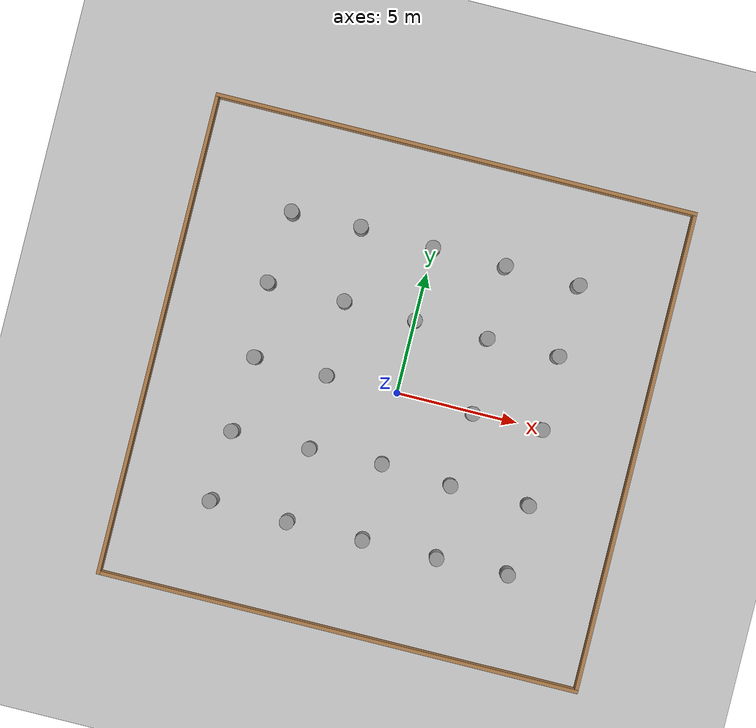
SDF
<sdf version='1.6'>
  <world name='default'>
    <!-- A global light source -->
    <include>
      <uri>model://sun</uri>
    </include>

    <!-- A ground plane -->
    <include>
      <uri>model://ground_plane</uri>
    </include>

    <physics type="ode">
      <real_time_update_rate>1000.0</real_time_update_rate>
      <max_step_size>0.001</max_step_size>
      <real_time_factor>1</real_time_factor>
      <ode>
        <solver>
          <type>quick</type>
          <iters>150</iters>
          <precon_iters>0</precon_iters>
          <sor>1.400000</sor>
          <use_dynamic_moi_rescaling>1</use_dynamic_moi_rescaling>
        </solver>
        <constraints>
          <cfm>0.00001</cfm>
          <erp>0.2</erp>
          <contact_max_correcting_vel>2000.000000</contact_max_correcting_vel>
          <contact_surface_layer>0.01000</contact_surface_layer>
        </constraints>
      </ode>
    </physics>

    <!-- Load world -->
    <include>
      <uri>model://columns_model</uri>
    </include>

    <scene>
      <ambient>0.4 0.4 0.4 1</ambient>
      <background>0.7 0.7 0.7 1</background>
      <shadows>true</shadows>
    </scene>

    <gui fullscreen='0'>
      <camera name='user_camera'>
        <pose>0.0 0.0 17.0 0 1.5708 0</pose>
        <view_controller>orbit</view_controller>
      </camera>
    </gui>
  </world>
</sdf>

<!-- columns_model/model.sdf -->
<sdf version='1.6'>
  <model name='columns_model'>
    <link name='Wall_0'>
      <pose frame=''>0 9.925 0 0 -0 0</pose>
      <self_collide>0</self_collide>
      <enable_wind>0</enable_wind>
      <kinematic>0</kinematic>
      <visual name='Wall_0_Visual'>
        <pose frame=''>0 0 0.25 0 -0 0</pose>
        <geometry>
          <box>
            <size>20 0.15 0.5</size>
          </box>
        </geometry>
        <material>
          <script>
            <uri>file://media/materials/scripts/gazebo.material</uri>
            <name>Gazebo/Wood</name>
          </script>
          <ambient>1 1 1 1</ambient>
        </material>
        <transparency>0</transparency>
        <cast_shadows>1</cast_shadows>
      </visual>
      <collision name='Wall_0_Collision'>
        <laser_retro>0</laser_retro>
        <max_contacts>10</max_contacts>
        <pose frame=''>0 0 0.25 0 -0 0</pose>
        <geometry>
          <box>
            <size>20 0.15 0.5</size>
          </box>
        </geometry>
        <surface>
          <friction>
            <ode>
              <mu>1</mu>
              <mu2>1</mu2>
              <fdir1>0 0 0</fdir1>
              <slip1>0</slip1>
              <slip2>0</slip2>
            </ode>
            <torsional>
              <coefficient>1</coefficient>
              <patch_radius>0</patch_radius>
              <surface_radius>0</surface_radius>
              <use_patch_radius>1</use_patch_radius>
              <ode>
                <slip>0</slip>
              </ode>
            </torsional>
          </friction>
          <bounce>
            <restitution_coefficient>0</restitution_coefficient>
            <threshold>1e+06</threshold>
          </bounce>
          <contact>
            <collide_without_contact>0</collide_without_contact>
            <collide_without_contact_bitmask>1</collide_without_contact_bitmask>
            <collide_bitmask>1</collide_bitmask>
            <ode>
              <soft_cfm>0</soft_cfm>
              <soft_erp>0.2</soft_erp>
              <kp>1e+13</kp>
              <kd>1</kd>
              <max_vel>0.01</max_vel>
              <min_depth>0</min_depth>
            </ode>
            <bullet>
              <split_impulse>1</split_impulse>
              <split_impulse_penetration_threshold>-0.01</split_impulse_penetration_threshold>
              <soft_cfm>0</soft_cfm>
              <soft_erp>0.2</soft_erp>
              <kp>1e+13</kp>
              <kd>1</kd>
            </bullet>
          </contact>
        </surface>
      </collision>
    </link>
    <link name='Wall_2'>
      <pose frame=''>-9.925 0 0 0 0 -1.5708</pose>
      <self_collide>0</self_collide>
      <enable_wind>0</enable_wind>
      <kinematic>0</kinematic>
      <visual name='Wall_2_Visual'>
        <pose frame=''>0 0 0.25 0 -0 0</pose>
        <geometry>
          <box>
            <size>20 0.15 0.5</size>
          </box>
        </geometry>
        <material>
          <script>
            <uri>file://media/materials/scripts/gazebo.material</uri>
            <name>Gazebo/Wood</name>
          </script>
          <ambient>1 1 1 1</ambient>
        </material>
        <transparency>0</transparency>
        <cast_shadows>1</cast_shadows>
      </visual>
      <collision name='Wall_2_Collision'>
        <laser_retro>0</laser_retro>
        <max_contacts>10</max_contacts>
        <pose frame=''>0 0 0.25 0 -0 0</pose>
        <geometry>
          <box>
            <size>20 0.15 0.5</size>
          </box>
        </geometry>
        <surface>
          <friction>
            <ode>
              <mu>1</mu>
              <mu2>1</mu2>
              <fdir1>0 0 0</fdir1>
              <slip1>0</slip1>
              <slip2>0</slip2>
            </ode>
            <torsional>
              <coefficient>1</coefficient>
              <patch_radius>0</patch_radius>
              <surface_radius>0</surface_radius>
              <use_patch_radius>1</use_patch_radius>
              <ode>
                <slip>0</slip>
              </ode>
            </torsional>
          </friction>
          <bounce>
            <restitution_coefficient>0</restitution_coefficient>
            <threshold>1e+06</threshold>
          </bounce>
          <contact>
            <collide_without_contact>0</collide_without_contact>
            <collide_without_contact_bitmask>1</collide_without_contact_bitmask>
            <collide_bitmask>1</collide_bitmask>
            <ode>
              <soft_cfm>0</soft_cfm>
              <soft_erp>0.2</soft_erp>
              <kp>1e+13</kp>
              <kd>1</kd>
              <max_vel>0.01</max_vel>
              <min_depth>0</min_depth>
            </ode>
            <bullet>
              <split_impulse>1</split_impulse>
              <split_impulse_penetration_threshold>-0.01</split_impulse_penetration_threshold>
              <soft_cfm>0</soft_cfm>
              <soft_erp>0.2</soft_erp>
              <kp>1e+13</kp>
              <kd>1</kd>
            </bullet>
          </contact>
        </surface>
      </collision>
    </link>
    <link name='Wall_3'>
      <pose frame=''>0 -9.925 0 0 -0 0</pose>
      <self_collide>0</self_collide>
      <enable_wind>0</enable_wind>
      <kinematic>0</kinematic>
      <visual name='Wall_3_Visual'>
        <pose frame=''>0 0 0.25 0 -0 0</pose>
        <geometry>
          <box>
            <size>20 0.15 0.5</size>
          </box>
        </geometry>
        <material>
          <script>
            <uri>file://media/materials/scripts/gazebo.material</uri>
            <name>Gazebo/Wood</name>
          </script>
          <ambient>1 1 1 1</ambient>
        </material>
        <transparency>0</transparency>
        <cast_shadows>1</cast_shadows>
      </visual>
      <collision name='Wall_3_Collision'>
        <laser_retro>0</laser_retro>
        <max_contacts>10</max_contacts>
        <pose frame=''>0 0 0.25 0 -0 0</pose>
        <geometry>
          <box>
            <size>20 0.15 0.5</size>
          </box>
        </geometry>
        <surface>
          <friction>
            <ode>
              <mu>1</mu>
              <mu2>1</mu2>
              <fdir1>0 0 0</fdir1>
              <slip1>0</slip1>
              <slip2>0</slip2>
            </ode>
            <torsional>
              <coefficient>1</coefficient>
              <patch_radius>0</patch_radius>
              <surface_radius>0</surface_radius>
              <use_patch_radius>1</use_patch_radius>
              <ode>
                <slip>0</slip>
              </ode>
            </torsional>
          </friction>
          <bounce>
            <restitution_coefficient>0</restitution_coefficient>
            <threshold>1e+06</threshold>
          </bounce>
          <contact>
            <collide_without_contact>0</collide_without_contact>
            <collide_without_contact_bitmask>1</collide_without_contact_bitmask>
            <collide_bitmask>1</collide_bitmask>
            <ode>
              <soft_cfm>0</soft_cfm>
              <soft_erp>0.2</soft_erp>
              <kp>1e+13</kp>
              <kd>1</kd>
              <max_vel>0.01</max_vel>
              <min_depth>0</min_depth>
            </ode>
            <bullet>
              <split_impulse>1</split_impulse>
              <split_impulse_penetration_threshold>-0.01</split_impulse_penetration_threshold>
              <soft_cfm>0</soft_cfm>
              <soft_erp>0.2</soft_erp>
              <kp>1e+13</kp>
              <kd>1</kd>
            </bullet>
          </contact>
        </surface>
      </collision>
    </link>
    <link name='Wall_4'>
      <pose frame=''>9.925 0 0 0 -0 1.5708</pose>
      <self_collide>0</self_collide>
      <enable_wind>0</enable_wind>
      <kinematic>0</kinematic>
      <visual name='Wall_4_Visual'>
        <pose frame=''>0 0 0.25 0 -0 0</pose>
        <geometry>
          <box>
            <size>20 0.15 0.5</size>
          </box>
        </geometry>
        <material>
          <script>
            <uri>file://media/materials/scripts/gazebo.material</uri>
            <name>Gazebo/Wood</name>
          </script>
          <ambient>1 1 1 1</ambient>
        </material>
        <transparency>0</transparency>
        <cast_shadows>1</cast_shadows>
      </visual>
      <collision name='Wall_4_Collision'>
        <laser_retro>0</laser_retro>
        <max_contacts>10</max_contacts>
        <pose frame=''>0 0 0.25 0 -0 0</pose>
        <geometry>
          <box>
            <size>20 0.15 0.5</size>
          </box>
        </geometry>
        <surface>
          <friction>
            <ode>
              <mu>1</mu>
              <mu2>1</mu2>
              <fdir1>0 0 0</fdir1>
              <slip1>0</slip1>
              <slip2>0</slip2>
            </ode>
            <torsional>
              <coefficient>1</coefficient>
              <patch_radius>0</patch_radius>
              <surface_radius>0</surface_radius>
              <use_patch_radius>1</use_patch_radius>
              <ode>
                <slip>0</slip>
              </ode>
            </torsional>
          </friction>
          <bounce>
            <restitution_coefficient>0</restitution_coefficient>
            <threshold>1e+06</threshold>
          </bounce>
          <contact>
            <collide_without_contact>0</collide_without_contact>
            <collide_without_contact_bitmask>1</collide_without_contact_bitmask>
            <collide_bitmask>1</collide_bitmask>
            <ode>
              <soft_cfm>0</soft_cfm>
              <soft_erp>0.2</soft_erp>
              <kp>1e+13</kp>
              <kd>1</kd>
              <max_vel>0.01</max_vel>
              <min_depth>0</min_depth>
            </ode>
            <bullet>
              <split_impulse>1</split_impulse>
              <split_impulse_penetration_threshold>-0.01</split_impulse_penetration_threshold>
              <soft_cfm>0</soft_cfm>
              <soft_erp>0.2</soft_erp>
              <kp>1e+13</kp>
              <kd>1</kd>
            </bullet>
          </contact>
        </surface>
      </collision>
    </link>
    <link name='link_0'>
      <inertial>
        <mass>1</mass>
        <inertia>
          <ixx>0.145833</ixx>
          <ixy>0</ixy>
          <ixz>0</ixz>
          <iyy>0.145833</iyy>
          <iyz>0</iyz>
          <izz>0.125</izz>
        </inertia>
        <pose frame=''>0 0 0 0 -0 0</pose>
      </inertial>
      <pose frame=''>0.107953 -2.9087 0.5 0 -0 0</pose>
      <gravity>1</gravity>
      <self_collide>0</self_collide>
      <kinematic>0</kinematic>
      <enable_wind>0</enable_wind>
      <visual name='visual'>
        <pose frame=''>0 0 0 0 -0 0</pose>
        <geometry>
          <cylinder>
            <radius>0.3</radius>
            <length>1</length>
          </cylinder>
        </geometry>
        <material>
          <lighting>1</lighting>
          <script>
            <uri>file://media/materials/scripts/gazebo.material</uri>
            <name>Gazebo/Grey</name>
          </script>
          <shader type='vertex'>
            <normal_map>__default__</normal_map>
          </shader>
          <ambient>0.3 0.3 0.3 1</ambient>
          <diffuse>0.7 0.7 0.7 1</diffuse>
          <specular>0.01 0.01 0.01 1</specular>
          <emissive>0 0 0 1</emissive>
        </material>
        <transparency>0</transparency>
        <cast_shadows>1</cast_shadows>
      </visual>
      <collision name='collision'>
        <laser_retro>0</laser_retro>
        <max_contacts>10</max_contacts>
        <pose frame=''>0 0 0 0 -0 0</pose>
        <geometry>
          <cylinder>
            <radius>0.3</radius>
            <length>1</length>
          </cylinder>
        </geometry>
        <surface>
          <friction>
            <ode>
              <mu>1</mu>
              <mu2>1</mu2>
              <fdir1>0 0 0</fdir1>
              <slip1>0</slip1>
              <slip2>0</slip2>
            </ode>
            <torsional>
              <coefficient>1</coefficient>
              <patch_radius>0</patch_radius>
              <surface_radius>0</surface_radius>
              <use_patch_radius>1</use_patch_radius>
              <ode>
                <slip>0</slip>
              </ode>
            </torsional>
          </friction>
          <bounce>
            <restitution_coefficient>0</restitution_coefficient>
            <threshold>1e+06</threshold>
          </bounce>
          <contact>
            <collide_without_contact>0</collide_without_contact>
            <collide_without_contact_bitmask>1</collide_without_contact_bitmask>
            <collide_bitmask>1</collide_bitmask>
            <ode>
              <soft_cfm>0</soft_cfm>
              <soft_erp>0.2</soft_erp>
              <kp>1e+13</kp>
              <kd>1</kd>
              <max_vel>0.01</max_vel>
              <min_depth>0</min_depth>
            </ode>
            <bullet>
              <split_impulse>1</split_impulse>
              <split_impulse_penetration_threshold>-0.01</split_impulse_penetration_threshold>
              <soft_cfm>0</soft_cfm>
              <soft_erp>0.2</soft_erp>
              <kp>1e+13</kp>
              <kd>1</kd>
            </bullet>
          </contact>
        </surface>
      </collision>
    </link>
    <link name='link_0_clone'>
      <inertial>
        <mass>1</mass>
        <inertia>
          <ixx>0.145833</ixx>
          <ixy>0</ixy>
          <ixz>0</ixz>
          <iyy>0.145833</iyy>
          <iyz>0</iyz>
          <izz>0.125</izz>
        </inertia>
        <pose frame=''>0 0 0 0 -0 0</pose>
      </inertial>
      <pose frame=''>0 3 0.5 0 -0 0</pose>
      <gravity>1</gravity>
      <self_collide>0</self_collide>
      <kinematic>0</kinematic>
      <enable_wind>0</enable_wind>
      <visual name='visual'>
        <pose frame=''>0 0 0 0 -0 0</pose>
        <geometry>
          <cylinder>
            <radius>0.3</radius>
            <length>1</length>
          </cylinder>
        </geometry>
        <material>
          <lighting>1</lighting>
          <script>
            <uri>file://media/materials/scripts/gazebo.material</uri>
            <name>Gazebo/Grey</name>
          </script>
          <shader type='vertex'>
            <normal_map>__default__</normal_map>
          </shader>
          <ambient>0.3 0.3 0.3 1</ambient>
          <diffuse>0.7 0.7 0.7 1</diffuse>
          <specular>0.01 0.01 0.01 1</specular>
          <emissive>0 0 0 1</emissive>
        </material>
        <transparency>0</transparency>
        <cast_shadows>1</cast_shadows>
      </visual>
      <collision name='collision'>
        <laser_retro>0</laser_retro>
        <max_contacts>10</max_contacts>
        <pose frame=''>0 0 0 0 -0 0</pose>
        <geometry>
          <cylinder>
            <radius>0.3</radius>
            <length>1</length>
          </cylinder>
        </geometry>
        <surface>
          <friction>
            <ode>
              <mu>1</mu>
              <mu2>1</mu2>
              <fdir1>0 0 0</fdir1>
              <slip1>0</slip1>
              <slip2>0</slip2>
            </ode>
            <torsional>
              <coefficient>1</coefficient>
              <patch_radius>0</patch_radius>
              <surface_radius>0</surface_radius>
              <use_patch_radius>1</use_patch_radius>
              <ode>
                <slip>0</slip>
              </ode>
            </torsional>
          </friction>
          <bounce>
            <restitution_coefficient>0</restitution_coefficient>
            <threshold>1e+06</threshold>
          </bounce>
          <contact>
            <collide_without_contact>0</collide_without_contact>
            <collide_without_contact_bitmask>1</collide_without_contact_bitmask>
            <collide_bitmask>1</collide_bitmask>
            <ode>
              <soft_cfm>0</soft_cfm>
              <soft_erp>0.2</soft_erp>
              <kp>1e+13</kp>
              <kd>1</kd>
              <max_vel>0.01</max_vel>
              <min_depth>0</min_depth>
            </ode>
            <bullet>
              <split_impulse>1</split_impulse>
              <split_impulse_penetration_threshold>-0.01</split_impulse_penetration_threshold>
              <soft_cfm>0</soft_cfm>
              <soft_erp>0.2</soft_erp>
              <kp>1e+13</kp>
              <kd>1</kd>
            </bullet>
          </contact>
        </surface>
      </collision>
    </link>
    <link name='link_0_clone_0'>
      <inertial>
        <mass>1</mass>
        <inertia>
          <ixx>0.145833</ixx>
          <ixy>0</ixy>
          <ixz>0</ixz>
          <iyy>0.145833</iyy>
          <iyz>0</iyz>
          <izz>0.125</izz>
        </inertia>
        <pose frame=''>0 0 0 0 -0 0</pose>
      </inertial>
      <pose frame=''>3.15995 -0.065507 0.5 0 -0 0</pose>
      <gravity>1</gravity>
      <self_collide>0</self_collide>
      <kinematic>0</kinematic>
      <enable_wind>0</enable_wind>
      <visual name='visual'>
        <pose frame=''>0 0 0 0 -0 0</pose>
        <geometry>
          <cylinder>
            <radius>0.3</radius>
            <length>1</length>
          </cylinder>
        </geometry>
        <material>
          <lighting>1</lighting>
          <script>
            <uri>file://media/materials/scripts/gazebo.material</uri>
            <name>Gazebo/Grey</name>
          </script>
          <shader type='vertex'>
            <normal_map>__default__</normal_map>
          </shader>
          <ambient>0.3 0.3 0.3 1</ambient>
          <diffuse>0.7 0.7 0.7 1</diffuse>
          <specular>0.01 0.01 0.01 1</specular>
          <emissive>0 0 0 1</emissive>
        </material>
        <transparency>0</transparency>
        <cast_shadows>1</cast_shadows>
      </visual>
      <collision name='collision'>
        <laser_retro>0</laser_retro>
        <max_contacts>10</max_contacts>
        <pose frame=''>0 0 0 0 -0 0</pose>
        <geometry>
          <cylinder>
            <radius>0.3</radius>
            <length>1</length>
          </cylinder>
        </geometry>
        <surface>
          <friction>
            <ode>
              <mu>1</mu>
              <mu2>1</mu2>
              <fdir1>0 0 0</fdir1>
              <slip1>0</slip1>
              <slip2>0</slip2>
            </ode>
            <torsional>
              <coefficient>1</coefficient>
              <patch_radius>0</patch_radius>
              <surface_radius>0</surface_radius>
              <use_patch_radius>1</use_patch_radius>
              <ode>
                <slip>0</slip>
              </ode>
            </torsional>
          </friction>
          <bounce>
            <restitution_coefficient>0</restitution_coefficient>
            <threshold>1e+06</threshold>
          </bounce>
          <contact>
            <collide_without_contact>0</collide_without_contact>
            <collide_without_contact_bitmask>1</collide_without_contact_bitmask>
            <collide_bitmask>1</collide_bitmask>
            <ode>
              <soft_cfm>0</soft_cfm>
              <soft_erp>0.2</soft_erp>
              <kp>1e+13</kp>
              <kd>1</kd>
              <max_vel>0.01</max_vel>
              <min_depth>0</min_depth>
            </ode>
            <bullet>
              <split_impulse>1</split_impulse>
              <split_impulse_penetration_threshold>-0.01</split_impulse_penetration_threshold>
              <soft_cfm>0</soft_cfm>
              <soft_erp>0.2</soft_erp>
              <kp>1e+13</kp>
              <kd>1</kd>
            </bullet>
          </contact>
        </surface>
      </collision>
    </link>
    <link name='link_0_clone_1'>
      <inertial>
        <mass>1</mass>
        <inertia>
          <ixx>0.145833</ixx>
          <ixy>0</ixy>
          <ixz>0</ixz>
          <iyy>0.145833</iyy>
          <iyz>0</iyz>
          <izz>0.125</izz>
        </inertia>
        <pose frame=''>0 0 0 0 -0 0</pose>
      </inertial>
      <pose frame=''>2.98902 -3.08623 0.5 0 -0 0</pose>
      <gravity>1</gravity>
      <self_collide>0</self_collide>
      <kinematic>0</kinematic>
      <enable_wind>0</enable_wind>
      <visual name='visual'>
        <pose frame=''>0 0 0 0 -0 0</pose>
        <geometry>
          <cylinder>
            <radius>0.3</radius>
            <length>1</length>
          </cylinder>
        </geometry>
        <material>
          <lighting>1</lighting>
          <script>
            <uri>file://media/materials/scripts/gazebo.material</uri>
            <name>Gazebo/Grey</name>
          </script>
          <shader type='vertex'>
            <normal_map>__default__</normal_map>
          </shader>
          <ambient>0.3 0.3 0.3 1</ambient>
          <diffuse>0.7 0.7 0.7 1</diffuse>
          <specular>0.01 0.01 0.01 1</specular>
          <emissive>0 0 0 1</emissive>
        </material>
        <transparency>0</transparency>
        <cast_shadows>1</cast_shadows>
      </visual>
      <collision name='collision'>
        <laser_retro>0</laser_retro>
        <max_contacts>10</max_contacts>
        <pose frame=''>0 0 0 0 -0 0</pose>
        <geometry>
          <cylinder>
            <radius>0.3</radius>
            <length>1</length>
          </cylinder>
        </geometry>
        <surface>
          <friction>
            <ode>
              <mu>1</mu>
              <mu2>1</mu2>
              <fdir1>0 0 0</fdir1>
              <slip1>0</slip1>
              <slip2>0</slip2>
            </ode>
            <torsional>
              <coefficient>1</coefficient>
              <patch_radius>0</patch_radius>
              <surface_radius>0</surface_radius>
              <use_patch_radius>1</use_patch_radius>
              <ode>
                <slip>0</slip>
              </ode>
            </torsional>
          </friction>
          <bounce>
            <restitution_coefficient>0</restitution_coefficient>
            <threshold>1e+06</threshold>
          </bounce>
          <contact>
            <collide_without_contact>0</collide_without_contact>
            <collide_without_contact_bitmask>1</collide_without_contact_bitmask>
            <collide_bitmask>1</collide_bitmask>
            <ode>
              <soft_cfm>0</soft_cfm>
              <soft_erp>0.2</soft_erp>
              <kp>1e+13</kp>
              <kd>1</kd>
              <max_vel>0.01</max_vel>
              <min_depth>0</min_depth>
            </ode>
            <bullet>
              <split_impulse>1</split_impulse>
              <split_impulse_penetration_threshold>-0.01</split_impulse_penetration_threshold>
              <soft_cfm>0</soft_cfm>
              <soft_erp>0.2</soft_erp>
              <kp>1e+13</kp>
              <kd>1</kd>
            </bullet>
          </contact>
        </surface>
      </collision>
    </link>
    <link name='link_0_clone_10'>
      <inertial>
        <mass>1</mass>
        <inertia>
          <ixx>0.145833</ixx>
          <ixy>0</ixy>
          <ixz>0</ixz>
          <iyy>0.145833</iyy>
          <iyz>0</iyz>
          <izz>0.125</izz>
        </inertia>
        <pose frame=''>0 0 0 0 -0 0</pose>
      </inertial>
      <pose frame=''>-6.22561 -6.00388 0.5 0 -0 0</pose>
      <gravity>1</gravity>
      <self_collide>0</self_collide>
      <kinematic>0</kinematic>
      <enable_wind>0</enable_wind>
      <visual name='visual'>
        <pose frame=''>0 0 0 0 -0 0</pose>
        <geometry>
          <cylinder>
            <radius>0.3</radius>
            <length>1</length>
          </cylinder>
        </geometry>
        <material>
          <lighting>1</lighting>
          <script>
            <uri>file://media/materials/scripts/gazebo.material</uri>
            <name>Gazebo/Grey</name>
          </script>
          <shader type='vertex'>
            <normal_map>__default__</normal_map>
          </shader>
          <ambient>0.3 0.3 0.3 1</ambient>
          <diffuse>0.7 0.7 0.7 1</diffuse>
          <specular>0.01 0.01 0.01 1</specular>
          <emissive>0 0 0 1</emissive>
        </material>
        <transparency>0</transparency>
        <cast_shadows>1</cast_shadows>
      </visual>
      <collision name='collision'>
        <laser_retro>0</laser_retro>
        <max_contacts>10</max_contacts>
        <pose frame=''>0 0 0 0 -0 0</pose>
        <geometry>
          <cylinder>
            <radius>0.3</radius>
            <length>1</length>
          </cylinder>
        </geometry>
        <surface>
          <friction>
            <ode>
              <mu>1</mu>
              <mu2>1</mu2>
              <fdir1>0 0 0</fdir1>
              <slip1>0</slip1>
              <slip2>0</slip2>
            </ode>
            <torsional>
              <coefficient>1</coefficient>
              <patch_radius>0</patch_radius>
              <surface_radius>0</surface_radius>
              <use_patch_radius>1</use_patch_radius>
              <ode>
                <slip>0</slip>
              </ode>
            </torsional>
          </friction>
          <bounce>
            <restitution_coefficient>0</restitution_coefficient>
            <threshold>1e+06</threshold>
          </bounce>
          <contact>
            <collide_without_contact>0</collide_without_contact>
            <collide_without_contact_bitmask>1</collide_without_contact_bitmask>
            <collide_bitmask>1</collide_bitmask>
            <ode>
              <soft_cfm>0</soft_cfm>
              <soft_erp>0.2</soft_erp>
              <kp>1e+13</kp>
              <kd>1</kd>
              <max_vel>0.01</max_vel>
              <min_depth>0</min_depth>
            </ode>
            <bullet>
              <split_impulse>1</split_impulse>
              <split_impulse_penetration_threshold>-0.01</split_impulse_penetration_threshold>
              <soft_cfm>0</soft_cfm>
              <soft_erp>0.2</soft_erp>
              <kp>1e+13</kp>
              <kd>1</kd>
            </bullet>
          </contact>
        </surface>
      </collision>
    </link>
    <link name='link_0_clone_11'>
      <inertial>
        <mass>1</mass>
        <inertia>
          <ixx>0.145833</ixx>
          <ixy>0</ixy>
          <ixz>0</ixz>
          <iyy>0.145833</iyy>
          <iyz>0</iyz>
          <izz>0.125</izz>
        </inertia>
        <pose frame=''>0 0 0 0 -0 0</pose>
      </inertial>
      <pose frame=''>-6.0599 -3.08284 0.5 0 -0 0</pose>
      <gravity>1</gravity>
      <self_collide>0</self_collide>
      <kinematic>0</kinematic>
      <enable_wind>0</enable_wind>
      <visual name='visual'>
        <pose frame=''>0 0 0 0 -0 0</pose>
        <geometry>
          <cylinder>
            <radius>0.3</radius>
            <length>1</length>
          </cylinder>
        </geometry>
        <material>
          <lighting>1</lighting>
          <script>
            <uri>file://media/materials/scripts/gazebo.material</uri>
            <name>Gazebo/Grey</name>
          </script>
          <shader type='vertex'>
            <normal_map>__default__</normal_map>
          </shader>
          <ambient>0.3 0.3 0.3 1</ambient>
          <diffuse>0.7 0.7 0.7 1</diffuse>
          <specular>0.01 0.01 0.01 1</specular>
          <emissive>0 0 0 1</emissive>
        </material>
        <transparency>0</transparency>
        <cast_shadows>1</cast_shadows>
      </visual>
      <collision name='collision'>
        <laser_retro>0</laser_retro>
        <max_contacts>10</max_contacts>
        <pose frame=''>0 0 0 0 -0 0</pose>
        <geometry>
          <cylinder>
            <radius>0.3</radius>
            <length>1</length>
          </cylinder>
        </geometry>
        <surface>
          <friction>
            <ode>
              <mu>1</mu>
              <mu2>1</mu2>
              <fdir1>0 0 0</fdir1>
              <slip1>0</slip1>
              <slip2>0</slip2>
            </ode>
            <torsional>
              <coefficient>1</coefficient>
              <patch_radius>0</patch_radius>
              <surface_radius>0</surface_radius>
              <use_patch_radius>1</use_patch_radius>
              <ode>
                <slip>0</slip>
              </ode>
            </torsional>
          </friction>
          <bounce>
            <restitution_coefficient>0</restitution_coefficient>
            <threshold>1e+06</threshold>
          </bounce>
          <contact>
            <collide_without_contact>0</collide_without_contact>
            <collide_without_contact_bitmask>1</collide_without_contact_bitmask>
            <collide_bitmask>1</collide_bitmask>
            <ode>
              <soft_cfm>0</soft_cfm>
              <soft_erp>0.2</soft_erp>
              <kp>1e+13</kp>
              <kd>1</kd>
              <max_vel>0.01</max_vel>
              <min_depth>0</min_depth>
            </ode>
            <bullet>
              <split_impulse>1</split_impulse>
              <split_impulse_penetration_threshold>-0.01</split_impulse_penetration_threshold>
              <soft_cfm>0</soft_cfm>
              <soft_erp>0.2</soft_erp>
              <kp>1e+13</kp>
              <kd>1</kd>
            </bullet>
          </contact>
        </surface>
      </collision>
    </link>
    <link name='link_0_clone_12'>
      <inertial>
        <mass>1</mass>
        <inertia>
          <ixx>0.145833</ixx>
          <ixy>0</ixy>
          <ixz>0</ixz>
          <iyy>0.145833</iyy>
          <iyz>0</iyz>
          <izz>0.125</izz>
        </inertia>
        <pose frame=''>0 0 0 0 -0 0</pose>
      </inertial>
      <pose frame=''>-5.89543 0.018668 0.5 0 -0 0</pose>
      <gravity>1</gravity>
      <self_collide>0</self_collide>
      <kinematic>0</kinematic>
      <enable_wind>0</enable_wind>
      <visual name='visual'>
        <pose frame=''>0 0 0 0 -0 0</pose>
        <geometry>
          <cylinder>
            <radius>0.3</radius>
            <length>1</length>
          </cylinder>
        </geometry>
        <material>
          <lighting>1</lighting>
          <script>
            <uri>file://media/materials/scripts/gazebo.material</uri>
            <name>Gazebo/Grey</name>
          </script>
          <shader type='vertex'>
            <normal_map>__default__</normal_map>
          </shader>
          <ambient>0.3 0.3 0.3 1</ambient>
          <diffuse>0.7 0.7 0.7 1</diffuse>
          <specular>0.01 0.01 0.01 1</specular>
          <emissive>0 0 0 1</emissive>
        </material>
        <transparency>0</transparency>
        <cast_shadows>1</cast_shadows>
      </visual>
      <collision name='collision'>
        <laser_retro>0</laser_retro>
        <max_contacts>10</max_contacts>
        <pose frame=''>0 0 0 0 -0 0</pose>
        <geometry>
          <cylinder>
            <radius>0.3</radius>
            <length>1</length>
          </cylinder>
        </geometry>
        <surface>
          <friction>
            <ode>
              <mu>1</mu>
              <mu2>1</mu2>
              <fdir1>0 0 0</fdir1>
              <slip1>0</slip1>
              <slip2>0</slip2>
            </ode>
            <torsional>
              <coefficient>1</coefficient>
              <patch_radius>0</patch_radius>
              <surface_radius>0</surface_radius>
              <use_patch_radius>1</use_patch_radius>
              <ode>
                <slip>0</slip>
              </ode>
            </torsional>
          </friction>
          <bounce>
            <restitution_coefficient>0</restitution_coefficient>
            <threshold>1e+06</threshold>
          </bounce>
          <contact>
            <collide_without_contact>0</collide_without_contact>
            <collide_without_contact_bitmask>1</collide_without_contact_bitmask>
            <collide_bitmask>1</collide_bitmask>
            <ode>
              <soft_cfm>0</soft_cfm>
              <soft_erp>0.2</soft_erp>
              <kp>1e+13</kp>
              <kd>1</kd>
              <max_vel>0.01</max_vel>
              <min_depth>0</min_depth>
            </ode>
            <bullet>
              <split_impulse>1</split_impulse>
              <split_impulse_penetration_threshold>-0.01</split_impulse_penetration_threshold>
              <soft_cfm>0</soft_cfm>
              <soft_erp>0.2</soft_erp>
              <kp>1e+13</kp>
              <kd>1</kd>
            </bullet>
          </contact>
        </surface>
      </collision>
    </link>
    <link name='link_0_clone_13'>
      <inertial>
        <mass>1</mass>
        <inertia>
          <ixx>0.145833</ixx>
          <ixy>0</ixy>
          <ixz>0</ixz>
          <iyy>0.145833</iyy>
          <iyz>0</iyz>
          <izz>0.125</izz>
        </inertia>
        <pose frame=''>0 0 0 0 -0 0</pose>
      </inertial>
      <pose frame=''>-6.09693 3.05557 0.5 0 -0 0</pose>
      <gravity>1</gravity>
      <self_collide>0</self_collide>
      <kinematic>0</kinematic>
      <enable_wind>0</enable_wind>
      <visual name='visual'>
        <pose frame=''>0 0 0 0 -0 0</pose>
        <geometry>
          <cylinder>
            <radius>0.3</radius>
            <length>1</length>
          </cylinder>
        </geometry>
        <material>
          <lighting>1</lighting>
          <script>
            <uri>file://media/materials/scripts/gazebo.material</uri>
            <name>Gazebo/Grey</name>
          </script>
          <shader type='vertex'>
            <normal_map>__default__</normal_map>
          </shader>
          <ambient>0.3 0.3 0.3 1</ambient>
          <diffuse>0.7 0.7 0.7 1</diffuse>
          <specular>0.01 0.01 0.01 1</specular>
          <emissive>0 0 0 1</emissive>
        </material>
        <transparency>0</transparency>
        <cast_shadows>1</cast_shadows>
      </visual>
      <collision name='collision'>
        <laser_retro>0</laser_retro>
        <max_contacts>10</max_contacts>
        <pose frame=''>0 0 0 0 -0 0</pose>
        <geometry>
          <cylinder>
            <radius>0.3</radius>
            <length>1</length>
          </cylinder>
        </geometry>
        <surface>
          <friction>
            <ode>
              <mu>1</mu>
              <mu2>1</mu2>
              <fdir1>0 0 0</fdir1>
              <slip1>0</slip1>
              <slip2>0</slip2>
            </ode>
            <torsional>
              <coefficient>1</coefficient>
              <patch_radius>0</patch_radius>
              <surface_radius>0</surface_radius>
              <use_patch_radius>1</use_patch_radius>
              <ode>
                <slip>0</slip>
              </ode>
            </torsional>
          </friction>
          <bounce>
            <restitution_coefficient>0</restitution_coefficient>
            <threshold>1e+06</threshold>
          </bounce>
          <contact>
            <collide_without_contact>0</collide_without_contact>
            <collide_without_contact_bitmask>1</collide_without_contact_bitmask>
            <collide_bitmask>1</collide_bitmask>
            <ode>
              <soft_cfm>0</soft_cfm>
              <soft_erp>0.2</soft_erp>
              <kp>1e+13</kp>
              <kd>1</kd>
              <max_vel>0.01</max_vel>
              <min_depth>0</min_depth>
            </ode>
            <bullet>
              <split_impulse>1</split_impulse>
              <split_impulse_penetration_threshold>-0.01</split_impulse_penetration_threshold>
              <soft_cfm>0</soft_cfm>
              <soft_erp>0.2</soft_erp>
              <kp>1e+13</kp>
              <kd>1</kd>
            </bullet>
          </contact>
        </surface>
      </collision>
    </link>
    <link name='link_0_clone_14'>
      <inertial>
        <mass>1</mass>
        <inertia>
          <ixx>0.145833</ixx>
          <ixy>0</ixy>
          <ixz>0</ixz>
          <iyy>0.145833</iyy>
          <iyz>0</iyz>
          <izz>0.125</izz>
        </inertia>
        <pose frame=''>0 0 0 0 -0 0</pose>
      </inertial>
      <pose frame=''>-5.85129 6.03455 0.5 0 -0 0</pose>
      <gravity>1</gravity>
      <self_collide>0</self_collide>
      <kinematic>0</kinematic>
      <enable_wind>0</enable_wind>
      <visual name='visual'>
        <pose frame=''>0 0 0 0 -0 0</pose>
        <geometry>
          <cylinder>
            <radius>0.3</radius>
            <length>1</length>
          </cylinder>
        </geometry>
        <material>
          <lighting>1</lighting>
          <script>
            <uri>file://media/materials/scripts/gazebo.material</uri>
            <name>Gazebo/Grey</name>
          </script>
          <shader type='vertex'>
            <normal_map>__default__</normal_map>
          </shader>
          <ambient>0.3 0.3 0.3 1</ambient>
          <diffuse>0.7 0.7 0.7 1</diffuse>
          <specular>0.01 0.01 0.01 1</specular>
          <emissive>0 0 0 1</emissive>
        </material>
        <transparency>0</transparency>
        <cast_shadows>1</cast_shadows>
      </visual>
      <collision name='collision'>
        <laser_retro>0</laser_retro>
        <max_contacts>10</max_contacts>
        <pose frame=''>0 0 0 0 -0 0</pose>
        <geometry>
          <cylinder>
            <radius>0.3</radius>
            <length>1</length>
          </cylinder>
        </geometry>
        <surface>
          <friction>
            <ode>
              <mu>1</mu>
              <mu2>1</mu2>
              <fdir1>0 0 0</fdir1>
              <slip1>0</slip1>
              <slip2>0</slip2>
            </ode>
            <torsional>
              <coefficient>1</coefficient>
              <patch_radius>0</patch_radius>
              <surface_radius>0</surface_radius>
              <use_patch_radius>1</use_patch_radius>
              <ode>
                <slip>0</slip>
              </ode>
            </torsional>
          </friction>
          <bounce>
            <restitution_coefficient>0</restitution_coefficient>
            <threshold>1e+06</threshold>
          </bounce>
          <contact>
            <collide_without_contact>0</collide_without_contact>
            <collide_without_contact_bitmask>1</collide_without_contact_bitmask>
            <collide_bitmask>1</collide_bitmask>
            <ode>
              <soft_cfm>0</soft_cfm>
              <soft_erp>0.2</soft_erp>
              <kp>1e+13</kp>
              <kd>1</kd>
              <max_vel>0.01</max_vel>
              <min_depth>0</min_depth>
            </ode>
            <bullet>
              <split_impulse>1</split_impulse>
              <split_impulse_penetration_threshold>-0.01</split_impulse_penetration_threshold>
              <soft_cfm>0</soft_cfm>
              <soft_erp>0.2</soft_erp>
              <kp>1e+13</kp>
              <kd>1</kd>
            </bullet>
          </contact>
        </surface>
      </collision>
    </link>
    <link name='link_0_clone_15'>
      <inertial>
        <mass>1</mass>
        <inertia>
          <ixx>0.145833</ixx>
          <ixy>0</ixy>
          <ixz>0</ixz>
          <iyy>0.145833</iyy>
          <iyz>0</iyz>
          <izz>0.125</izz>
        </inertia>
        <pose frame=''>0 0 0 0 -0 0</pose>
      </inertial>
      <pose frame=''>-3.00934 6.11637 0.5 0 -0 0</pose>
      <gravity>1</gravity>
      <self_collide>0</self_collide>
      <kinematic>0</kinematic>
      <enable_wind>0</enable_wind>
      <visual name='visual'>
        <pose frame=''>0 0 0 0 -0 0</pose>
        <geometry>
          <cylinder>
            <radius>0.3</radius>
            <length>1</length>
          </cylinder>
        </geometry>
        <material>
          <lighting>1</lighting>
          <script>
            <uri>file://media/materials/scripts/gazebo.material</uri>
            <name>Gazebo/Grey</name>
          </script>
          <shader type='vertex'>
            <normal_map>__default__</normal_map>
          </shader>
          <ambient>0.3 0.3 0.3 1</ambient>
          <diffuse>0.7 0.7 0.7 1</diffuse>
          <specular>0.01 0.01 0.01 1</specular>
          <emissive>0 0 0 1</emissive>
        </material>
        <transparency>0</transparency>
        <cast_shadows>1</cast_shadows>
      </visual>
      <collision name='collision'>
        <laser_retro>0</laser_retro>
        <max_contacts>10</max_contacts>
        <pose frame=''>0 0 0 0 -0 0</pose>
        <geometry>
          <cylinder>
            <radius>0.3</radius>
            <length>1</length>
          </cylinder>
        </geometry>
        <surface>
          <friction>
            <ode>
              <mu>1</mu>
              <mu2>1</mu2>
              <fdir1>0 0 0</fdir1>
              <slip1>0</slip1>
              <slip2>0</slip2>
            </ode>
            <torsional>
              <coefficient>1</coefficient>
              <patch_radius>0</patch_radius>
              <surface_radius>0</surface_radius>
              <use_patch_radius>1</use_patch_radius>
              <ode>
                <slip>0</slip>
              </ode>
            </torsional>
          </friction>
          <bounce>
            <restitution_coefficient>0</restitution_coefficient>
            <threshold>1e+06</threshold>
          </bounce>
          <contact>
            <collide_without_contact>0</collide_without_contact>
            <collide_without_contact_bitmask>1</collide_without_contact_bitmask>
            <collide_bitmask>1</collide_bitmask>
            <ode>
              <soft_cfm>0</soft_cfm>
              <soft_erp>0.2</soft_erp>
              <kp>1e+13</kp>
              <kd>1</kd>
              <max_vel>0.01</max_vel>
              <min_depth>0</min_depth>
            </ode>
            <bullet>
              <split_impulse>1</split_impulse>
              <split_impulse_penetration_threshold>-0.01</split_impulse_penetration_threshold>
              <soft_cfm>0</soft_cfm>
              <soft_erp>0.2</soft_erp>
              <kp>1e+13</kp>
              <kd>1</kd>
            </bullet>
          </contact>
        </surface>
      </collision>
    </link>
    <link name='link_0_clone_16'>
      <inertial>
        <mass>1</mass>
        <inertia>
          <ixx>0.145833</ixx>
          <ixy>0</ixy>
          <ixz>0</ixz>
          <iyy>0.145833</iyy>
          <iyz>0</iyz>
          <izz>0.125</izz>
        </inertia>
        <pose frame=''>0 0 0 0 -0 0</pose>
      </inertial>
      <pose frame=''>0 6 0.5 0 -0 0</pose>
      <gravity>1</gravity>
      <self_collide>0</self_collide>
      <kinematic>0</kinematic>
      <enable_wind>0</enable_wind>
      <visual name='visual'>
        <pose frame=''>0 0 0 0 -0 0</pose>
        <geometry>
          <cylinder>
            <radius>0.3</radius>
            <length>1</length>
          </cylinder>
        </geometry>
        <material>
          <lighting>1</lighting>
          <script>
            <uri>file://media/materials/scripts/gazebo.material</uri>
            <name>Gazebo/Grey</name>
          </script>
          <shader type='vertex'>
            <normal_map>__default__</normal_map>
          </shader>
          <ambient>0.3 0.3 0.3 1</ambient>
          <diffuse>0.7 0.7 0.7 1</diffuse>
          <specular>0.01 0.01 0.01 1</specular>
          <emissive>0 0 0 1</emissive>
        </material>
        <transparency>0</transparency>
        <cast_shadows>1</cast_shadows>
      </visual>
      <collision name='collision'>
        <laser_retro>0</laser_retro>
        <max_contacts>10</max_contacts>
        <pose frame=''>0 0 0 0 -0 0</pose>
        <geometry>
          <cylinder>
            <radius>0.3</radius>
            <length>1</length>
          </cylinder>
        </geometry>
        <surface>
          <friction>
            <ode>
              <mu>1</mu>
              <mu2>1</mu2>
              <fdir1>0 0 0</fdir1>
              <slip1>0</slip1>
              <slip2>0</slip2>
            </ode>
            <torsional>
              <coefficient>1</coefficient>
              <patch_radius>0</patch_radius>
              <surface_radius>0</surface_radius>
              <use_patch_radius>1</use_patch_radius>
              <ode>
                <slip>0</slip>
              </ode>
            </torsional>
          </friction>
          <bounce>
            <restitution_coefficient>0</restitution_coefficient>
            <threshold>1e+06</threshold>
          </bounce>
          <contact>
            <collide_without_contact>0</collide_without_contact>
            <collide_without_contact_bitmask>1</collide_without_contact_bitmask>
            <collide_bitmask>1</collide_bitmask>
            <ode>
              <soft_cfm>0</soft_cfm>
              <soft_erp>0.2</soft_erp>
              <kp>1e+13</kp>
              <kd>1</kd>
              <max_vel>0.01</max_vel>
              <min_depth>0</min_depth>
            </ode>
            <bullet>
              <split_impulse>1</split_impulse>
              <split_impulse_penetration_threshold>-0.01</split_impulse_penetration_threshold>
              <soft_cfm>0</soft_cfm>
              <soft_erp>0.2</soft_erp>
              <kp>1e+13</kp>
              <kd>1</kd>
            </bullet>
          </contact>
        </surface>
      </collision>
    </link>
    <link name='link_0_clone_17'>
      <inertial>
        <mass>1</mass>
        <inertia>
          <ixx>0.145833</ixx>
          <ixy>0</ixy>
          <ixz>0</ixz>
          <iyy>0.145833</iyy>
          <iyz>0</iyz>
          <izz>0.125</izz>
        </inertia>
        <pose frame=''>0 0 0 0 -0 0</pose>
      </inertial>
      <pose frame=''>3 6 0.5 0 -0 0</pose>
      <gravity>1</gravity>
      <self_collide>0</self_collide>
      <kinematic>0</kinematic>
      <enable_wind>0</enable_wind>
      <visual name='visual'>
        <pose frame=''>0 0 0 0 -0 0</pose>
        <geometry>
          <cylinder>
            <radius>0.3</radius>
            <length>1</length>
          </cylinder>
        </geometry>
        <material>
          <lighting>1</lighting>
          <script>
            <uri>file://media/materials/scripts/gazebo.material</uri>
            <name>Gazebo/Grey</name>
          </script>
          <shader type='vertex'>
            <normal_map>__default__</normal_map>
          </shader>
          <ambient>0.3 0.3 0.3 1</ambient>
          <diffuse>0.7 0.7 0.7 1</diffuse>
          <specular>0.01 0.01 0.01 1</specular>
          <emissive>0 0 0 1</emissive>
        </material>
        <transparency>0</transparency>
        <cast_shadows>1</cast_shadows>
      </visual>
      <collision name='collision'>
        <laser_retro>0</laser_retro>
        <max_contacts>10</max_contacts>
        <pose frame=''>0 0 0 0 -0 0</pose>
        <geometry>
          <cylinder>
            <radius>0.3</radius>
            <length>1</length>
          </cylinder>
        </geometry>
        <surface>
          <friction>
            <ode>
              <mu>1</mu>
              <mu2>1</mu2>
              <fdir1>0 0 0</fdir1>
              <slip1>0</slip1>
              <slip2>0</slip2>
            </ode>
            <torsional>
              <coefficient>1</coefficient>
              <patch_radius>0</patch_radius>
              <surface_radius>0</surface_radius>
              <use_patch_radius>1</use_patch_radius>
              <ode>
                <slip>0</slip>
              </ode>
            </torsional>
          </friction>
          <bounce>
            <restitution_coefficient>0</restitution_coefficient>
            <threshold>1e+06</threshold>
          </bounce>
          <contact>
            <collide_without_contact>0</collide_without_contact>
            <collide_without_contact_bitmask>1</collide_without_contact_bitmask>
            <collide_bitmask>1</collide_bitmask>
            <ode>
              <soft_cfm>0</soft_cfm>
              <soft_erp>0.2</soft_erp>
              <kp>1e+13</kp>
              <kd>1</kd>
              <max_vel>0.01</max_vel>
              <min_depth>0</min_depth>
            </ode>
            <bullet>
              <split_impulse>1</split_impulse>
              <split_impulse_penetration_threshold>-0.01</split_impulse_penetration_threshold>
              <soft_cfm>0</soft_cfm>
              <soft_erp>0.2</soft_erp>
              <kp>1e+13</kp>
              <kd>1</kd>
            </bullet>
          </contact>
        </surface>
      </collision>
    </link>
    <link name='link_0_clone_18'>
      <inertial>
        <mass>1</mass>
        <inertia>
          <ixx>0.145833</ixx>
          <ixy>0</ixy>
          <ixz>0</ixz>
          <iyy>0.145833</iyy>
          <iyz>0</iyz>
          <izz>0.125</izz>
        </inertia>
        <pose frame=''>0 0 0 0 -0 0</pose>
      </inertial>
      <pose frame=''>6.22974 -3.10295 0.5 0 -0 0</pose>
      <gravity>1</gravity>
      <self_collide>0</self_collide>
      <kinematic>0</kinematic>
      <enable_wind>0</enable_wind>
      <visual name='visual'>
        <pose frame=''>0 0 0 0 -0 0</pose>
        <geometry>
          <cylinder>
            <radius>0.3</radius>
            <length>1</length>
          </cylinder>
        </geometry>
        <material>
          <lighting>1</lighting>
          <script>
            <uri>file://media/materials/scripts/gazebo.material</uri>
            <name>Gazebo/Grey</name>
          </script>
          <shader type='vertex'>
            <normal_map>__default__</normal_map>
          </shader>
          <ambient>0.3 0.3 0.3 1</ambient>
          <diffuse>0.7 0.7 0.7 1</diffuse>
          <specular>0.01 0.01 0.01 1</specular>
          <emissive>0 0 0 1</emissive>
        </material>
        <transparency>0</transparency>
        <cast_shadows>1</cast_shadows>
      </visual>
      <collision name='collision'>
        <laser_retro>0</laser_retro>
        <max_contacts>10</max_contacts>
        <pose frame=''>0 0 0 0 -0 0</pose>
        <geometry>
          <cylinder>
            <radius>0.3</radius>
            <length>1</length>
          </cylinder>
        </geometry>
        <surface>
          <friction>
            <ode>
              <mu>1</mu>
              <mu2>1</mu2>
              <fdir1>0 0 0</fdir1>
              <slip1>0</slip1>
              <slip2>0</slip2>
            </ode>
            <torsional>
              <coefficient>1</coefficient>
              <patch_radius>0</patch_radius>
              <surface_radius>0</surface_radius>
              <use_patch_radius>1</use_patch_radius>
              <ode>
                <slip>0</slip>
              </ode>
            </torsional>
          </friction>
          <bounce>
            <restitution_coefficient>0</restitution_coefficient>
            <threshold>1e+06</threshold>
          </bounce>
          <contact>
            <collide_without_contact>0</collide_without_contact>
            <collide_without_contact_bitmask>1</collide_without_contact_bitmask>
            <collide_bitmask>1</collide_bitmask>
            <ode>
              <soft_cfm>0</soft_cfm>
              <soft_erp>0.2</soft_erp>
              <kp>1e+13</kp>
              <kd>1</kd>
              <max_vel>0.01</max_vel>
              <min_depth>0</min_depth>
            </ode>
            <bullet>
              <split_impulse>1</split_impulse>
              <split_impulse_penetration_threshold>-0.01</split_impulse_penetration_threshold>
              <soft_cfm>0</soft_cfm>
              <soft_erp>0.2</soft_erp>
              <kp>1e+13</kp>
              <kd>1</kd>
            </bullet>
          </contact>
        </surface>
      </collision>
    </link>
    <link name='link_0_clone_19'>
      <inertial>
        <mass>1</mass>
        <inertia>
          <ixx>0.145833</ixx>
          <ixy>0</ixy>
          <ixz>0</ixz>
          <iyy>0.145833</iyy>
          <iyz>0</iyz>
          <izz>0.125</izz>
        </inertia>
        <pose frame=''>0 0 0 0 -0 0</pose>
      </inertial>
      <pose frame=''>6.01692 -0.020745 0.5 0 -0 0</pose>
      <gravity>1</gravity>
      <self_collide>0</self_collide>
      <kinematic>0</kinematic>
      <enable_wind>0</enable_wind>
      <visual name='visual'>
        <pose frame=''>0 0 0 0 -0 0</pose>
        <geometry>
          <cylinder>
            <radius>0.3</radius>
            <length>1</length>
          </cylinder>
        </geometry>
        <material>
          <lighting>1</lighting>
          <script>
            <uri>file://media/materials/scripts/gazebo.material</uri>
            <name>Gazebo/Grey</name>
          </script>
          <shader type='vertex'>
            <normal_map>__default__</normal_map>
          </shader>
          <ambient>0.3 0.3 0.3 1</ambient>
          <diffuse>0.7 0.7 0.7 1</diffuse>
          <specular>0.01 0.01 0.01 1</specular>
          <emissive>0 0 0 1</emissive>
        </material>
        <transparency>0</transparency>
        <cast_shadows>1</cast_shadows>
      </visual>
      <collision name='collision'>
        <laser_retro>0</laser_retro>
        <max_contacts>10</max_contacts>
        <pose frame=''>0 0 0 0 -0 0</pose>
        <geometry>
          <cylinder>
            <radius>0.3</radius>
            <length>1</length>
          </cylinder>
        </geometry>
        <surface>
          <friction>
            <ode>
              <mu>1</mu>
              <mu2>1</mu2>
              <fdir1>0 0 0</fdir1>
              <slip1>0</slip1>
              <slip2>0</slip2>
            </ode>
            <torsional>
              <coefficient>1</coefficient>
              <patch_radius>0</patch_radius>
              <surface_radius>0</surface_radius>
              <use_patch_radius>1</use_patch_radius>
              <ode>
                <slip>0</slip>
              </ode>
            </torsional>
          </friction>
          <bounce>
            <restitution_coefficient>0</restitution_coefficient>
            <threshold>1e+06</threshold>
          </bounce>
          <contact>
            <collide_without_contact>0</collide_without_contact>
            <collide_without_contact_bitmask>1</collide_without_contact_bitmask>
            <collide_bitmask>1</collide_bitmask>
            <ode>
              <soft_cfm>0</soft_cfm>
              <soft_erp>0.2</soft_erp>
              <kp>1e+13</kp>
              <kd>1</kd>
              <max_vel>0.01</max_vel>
              <min_depth>0</min_depth>
            </ode>
            <bullet>
              <split_impulse>1</split_impulse>
              <split_impulse_penetration_threshold>-0.01</split_impulse_penetration_threshold>
              <soft_cfm>0</soft_cfm>
              <soft_erp>0.2</soft_erp>
              <kp>1e+13</kp>
              <kd>1</kd>
            </bullet>
          </contact>
        </surface>
      </collision>
    </link>
    <link name='link_0_clone_2'>
      <inertial>
        <mass>1</mass>
        <inertia>
          <ixx>0.145833</ixx>
          <ixy>0</ixy>
          <ixz>0</ixz>
          <iyy>0.145833</iyy>
          <iyz>0</iyz>
          <izz>0.125</izz>
        </inertia>
        <pose frame=''>0 0 0 0 -0 0</pose>
      </inertial>
      <pose frame=''>-2.86952 -3.01769 0.5 0 -0 0</pose>
      <gravity>1</gravity>
      <self_collide>0</self_collide>
      <kinematic>0</kinematic>
      <enable_wind>0</enable_wind>
      <visual name='visual'>
        <pose frame=''>0 0 0 0 -0 0</pose>
        <geometry>
          <cylinder>
            <radius>0.3</radius>
            <length>1</length>
          </cylinder>
        </geometry>
        <material>
          <lighting>1</lighting>
          <script>
            <uri>file://media/materials/scripts/gazebo.material</uri>
            <name>Gazebo/Grey</name>
          </script>
          <shader type='vertex'>
            <normal_map>__default__</normal_map>
          </shader>
          <ambient>0.3 0.3 0.3 1</ambient>
          <diffuse>0.7 0.7 0.7 1</diffuse>
          <specular>0.01 0.01 0.01 1</specular>
          <emissive>0 0 0 1</emissive>
        </material>
        <transparency>0</transparency>
        <cast_shadows>1</cast_shadows>
      </visual>
      <collision name='collision'>
        <laser_retro>0</laser_retro>
        <max_contacts>10</max_contacts>
        <pose frame=''>0 0 0 0 -0 0</pose>
        <geometry>
          <cylinder>
            <radius>0.3</radius>
            <length>1</length>
          </cylinder>
        </geometry>
        <surface>
          <friction>
            <ode>
              <mu>1</mu>
              <mu2>1</mu2>
              <fdir1>0 0 0</fdir1>
              <slip1>0</slip1>
              <slip2>0</slip2>
            </ode>
            <torsional>
              <coefficient>1</coefficient>
              <patch_radius>0</patch_radius>
              <surface_radius>0</surface_radius>
              <use_patch_radius>1</use_patch_radius>
              <ode>
                <slip>0</slip>
              </ode>
            </torsional>
          </friction>
          <bounce>
            <restitution_coefficient>0</restitution_coefficient>
            <threshold>1e+06</threshold>
          </bounce>
          <contact>
            <collide_without_contact>0</collide_without_contact>
            <collide_without_contact_bitmask>1</collide_without_contact_bitmask>
            <collide_bitmask>1</collide_bitmask>
            <ode>
              <soft_cfm>0</soft_cfm>
              <soft_erp>0.2</soft_erp>
              <kp>1e+13</kp>
              <kd>1</kd>
              <max_vel>0.01</max_vel>
              <min_depth>0</min_depth>
            </ode>
            <bullet>
              <split_impulse>1</split_impulse>
              <split_impulse_penetration_threshold>-0.01</split_impulse_penetration_threshold>
              <soft_cfm>0</soft_cfm>
              <soft_erp>0.2</soft_erp>
              <kp>1e+13</kp>
              <kd>1</kd>
            </bullet>
          </contact>
        </surface>
      </collision>
    </link>
    <link name='link_0_clone_20'>
      <inertial>
        <mass>1</mass>
        <inertia>
          <ixx>0.145833</ixx>
          <ixy>0</ixy>
          <ixz>0</ixz>
          <iyy>0.145833</iyy>
          <iyz>0</iyz>
          <izz>0.125</izz>
        </inertia>
        <pose frame=''>0 0 0 0 -0 0</pose>
      </inertial>
      <pose frame=''>5.9482 3.00244 0.5 0 -0 0</pose>
      <gravity>1</gravity>
      <self_collide>0</self_collide>
      <kinematic>0</kinematic>
      <enable_wind>0</enable_wind>
      <visual name='visual'>
        <pose frame=''>0 0 0 0 -0 0</pose>
        <geometry>
          <cylinder>
            <radius>0.3</radius>
            <length>1</length>
          </cylinder>
        </geometry>
        <material>
          <lighting>1</lighting>
          <script>
            <uri>file://media/materials/scripts/gazebo.material</uri>
            <name>Gazebo/Grey</name>
          </script>
          <shader type='vertex'>
            <normal_map>__default__</normal_map>
          </shader>
          <ambient>0.3 0.3 0.3 1</ambient>
          <diffuse>0.7 0.7 0.7 1</diffuse>
          <specular>0.01 0.01 0.01 1</specular>
          <emissive>0 0 0 1</emissive>
        </material>
        <transparency>0</transparency>
        <cast_shadows>1</cast_shadows>
      </visual>
      <collision name='collision'>
        <laser_retro>0</laser_retro>
        <max_contacts>10</max_contacts>
        <pose frame=''>0 0 0 0 -0 0</pose>
        <geometry>
          <cylinder>
            <radius>0.3</radius>
            <length>1</length>
          </cylinder>
        </geometry>
        <surface>
          <friction>
            <ode>
              <mu>1</mu>
              <mu2>1</mu2>
              <fdir1>0 0 0</fdir1>
              <slip1>0</slip1>
              <slip2>0</slip2>
            </ode>
            <torsional>
              <coefficient>1</coefficient>
              <patch_radius>0</patch_radius>
              <surface_radius>0</surface_radius>
              <use_patch_radius>1</use_patch_radius>
              <ode>
                <slip>0</slip>
              </ode>
            </torsional>
          </friction>
          <bounce>
            <restitution_coefficient>0</restitution_coefficient>
            <threshold>1e+06</threshold>
          </bounce>
          <contact>
            <collide_without_contact>0</collide_without_contact>
            <collide_without_contact_bitmask>1</collide_without_contact_bitmask>
            <collide_bitmask>1</collide_bitmask>
            <ode>
              <soft_cfm>0</soft_cfm>
              <soft_erp>0.2</soft_erp>
              <kp>1e+13</kp>
              <kd>1</kd>
              <max_vel>0.01</max_vel>
              <min_depth>0</min_depth>
            </ode>
            <bullet>
              <split_impulse>1</split_impulse>
              <split_impulse_penetration_threshold>-0.01</split_impulse_penetration_threshold>
              <soft_cfm>0</soft_cfm>
              <soft_erp>0.2</soft_erp>
              <kp>1e+13</kp>
              <kd>1</kd>
            </bullet>
          </contact>
        </surface>
      </collision>
    </link>
    <link name='link_0_clone_21'>
      <inertial>
        <mass>1</mass>
        <inertia>
          <ixx>0.145833</ixx>
          <ixy>0</ixy>
          <ixz>0</ixz>
          <iyy>0.145833</iyy>
          <iyz>0</iyz>
          <izz>0.125</izz>
        </inertia>
        <pose frame=''>0 0 0 0 -0 0</pose>
      </inertial>
      <pose frame=''>6.04932 5.9593 0.5 0 -0 0</pose>
      <gravity>1</gravity>
      <self_collide>0</self_collide>
      <kinematic>0</kinematic>
      <enable_wind>0</enable_wind>
      <visual name='visual'>
        <pose frame=''>0 0 0 0 -0 0</pose>
        <geometry>
          <cylinder>
            <radius>0.3</radius>
            <length>1</length>
          </cylinder>
        </geometry>
        <material>
          <lighting>1</lighting>
          <script>
            <uri>file://media/materials/scripts/gazebo.material</uri>
            <name>Gazebo/Grey</name>
          </script>
          <shader type='vertex'>
            <normal_map>__default__</normal_map>
          </shader>
          <ambient>0.3 0.3 0.3 1</ambient>
          <diffuse>0.7 0.7 0.7 1</diffuse>
          <specular>0.01 0.01 0.01 1</specular>
          <emissive>0 0 0 1</emissive>
        </material>
        <transparency>0</transparency>
        <cast_shadows>1</cast_shadows>
      </visual>
      <collision name='collision'>
        <laser_retro>0</laser_retro>
        <max_contacts>10</max_contacts>
        <pose frame=''>0 0 0 0 -0 0</pose>
        <geometry>
          <cylinder>
            <radius>0.3</radius>
            <length>1</length>
          </cylinder>
        </geometry>
        <surface>
          <friction>
            <ode>
              <mu>1</mu>
              <mu2>1</mu2>
              <fdir1>0 0 0</fdir1>
              <slip1>0</slip1>
              <slip2>0</slip2>
            </ode>
            <torsional>
              <coefficient>1</coefficient>
              <patch_radius>0</patch_radius>
              <surface_radius>0</surface_radius>
              <use_patch_radius>1</use_patch_radius>
              <ode>
                <slip>0</slip>
              </ode>
            </torsional>
          </friction>
          <bounce>
            <restitution_coefficient>0</restitution_coefficient>
            <threshold>1e+06</threshold>
          </bounce>
          <contact>
            <collide_without_contact>0</collide_without_contact>
            <collide_without_contact_bitmask>1</collide_without_contact_bitmask>
            <collide_bitmask>1</collide_bitmask>
            <ode>
              <soft_cfm>0</soft_cfm>
              <soft_erp>0.2</soft_erp>
              <kp>1e+13</kp>
              <kd>1</kd>
              <max_vel>0.01</max_vel>
              <min_depth>0</min_depth>
            </ode>
            <bullet>
              <split_impulse>1</split_impulse>
              <split_impulse_penetration_threshold>-0.01</split_impulse_penetration_threshold>
              <soft_cfm>0</soft_cfm>
              <soft_erp>0.2</soft_erp>
              <kp>1e+13</kp>
              <kd>1</kd>
            </bullet>
          </contact>
        </surface>
      </collision>
    </link>
    <link name='link_0_clone_3'>
      <inertial>
        <mass>1</mass>
        <inertia>
          <ixx>0.145833</ixx>
          <ixy>0</ixy>
          <ixz>0</ixz>
          <iyy>0.145833</iyy>
          <iyz>0</iyz>
          <izz>0.125</izz>
        </inertia>
        <pose frame=''>0 0 0 0 -0 0</pose>
      </inertial>
      <pose frame=''>-2.9057 -0.004791 0.5 0 -0 0</pose>
      <gravity>1</gravity>
      <self_collide>0</self_collide>
      <kinematic>0</kinematic>
      <enable_wind>0</enable_wind>
      <visual name='visual'>
        <pose frame=''>0 0 0 0 -0 0</pose>
        <geometry>
          <cylinder>
            <radius>0.3</radius>
            <length>1</length>
          </cylinder>
        </geometry>
        <material>
          <lighting>1</lighting>
          <script>
            <uri>file://media/materials/scripts/gazebo.material</uri>
            <name>Gazebo/Grey</name>
          </script>
          <shader type='vertex'>
            <normal_map>__default__</normal_map>
          </shader>
          <ambient>0.3 0.3 0.3 1</ambient>
          <diffuse>0.7 0.7 0.7 1</diffuse>
          <specular>0.01 0.01 0.01 1</specular>
          <emissive>0 0 0 1</emissive>
        </material>
        <transparency>0</transparency>
        <cast_shadows>1</cast_shadows>
      </visual>
      <collision name='collision'>
        <laser_retro>0</laser_retro>
        <max_contacts>10</max_contacts>
        <pose frame=''>0 0 0 0 -0 0</pose>
        <geometry>
          <cylinder>
            <radius>0.3</radius>
            <length>1</length>
          </cylinder>
        </geometry>
        <surface>
          <friction>
            <ode>
              <mu>1</mu>
              <mu2>1</mu2>
              <fdir1>0 0 0</fdir1>
              <slip1>0</slip1>
              <slip2>0</slip2>
            </ode>
            <torsional>
              <coefficient>1</coefficient>
              <patch_radius>0</patch_radius>
              <surface_radius>0</surface_radius>
              <use_patch_radius>1</use_patch_radius>
              <ode>
                <slip>0</slip>
              </ode>
            </torsional>
          </friction>
          <bounce>
            <restitution_coefficient>0</restitution_coefficient>
            <threshold>1e+06</threshold>
          </bounce>
          <contact>
            <collide_without_contact>0</collide_without_contact>
            <collide_without_contact_bitmask>1</collide_without_contact_bitmask>
            <collide_bitmask>1</collide_bitmask>
            <ode>
              <soft_cfm>0</soft_cfm>
              <soft_erp>0.2</soft_erp>
              <kp>1e+13</kp>
              <kd>1</kd>
              <max_vel>0.01</max_vel>
              <min_depth>0</min_depth>
            </ode>
            <bullet>
              <split_impulse>1</split_impulse>
              <split_impulse_penetration_threshold>-0.01</split_impulse_penetration_threshold>
              <soft_cfm>0</soft_cfm>
              <soft_erp>0.2</soft_erp>
              <kp>1e+13</kp>
              <kd>1</kd>
            </bullet>
          </contact>
        </surface>
      </collision>
    </link>
    <link name='link_0_clone_4'>
      <inertial>
        <mass>1</mass>
        <inertia>
          <ixx>0.145833</ixx>
          <ixy>0</ixy>
          <ixz>0</ixz>
          <iyy>0.145833</iyy>
          <iyz>0</iyz>
          <izz>0.125</izz>
        </inertia>
        <pose frame=''>0 0 0 0 -0 0</pose>
      </inertial>
      <pose frame=''>-2.93435 3.06427 0.5 0 -0 0</pose>
      <gravity>1</gravity>
      <self_collide>0</self_collide>
      <kinematic>0</kinematic>
      <enable_wind>0</enable_wind>
      <visual name='visual'>
        <pose frame=''>0 0 0 0 -0 0</pose>
        <geometry>
          <cylinder>
            <radius>0.3</radius>
            <length>1</length>
          </cylinder>
        </geometry>
        <material>
          <lighting>1</lighting>
          <script>
            <uri>file://media/materials/scripts/gazebo.material</uri>
            <name>Gazebo/Grey</name>
          </script>
          <shader type='vertex'>
            <normal_map>__default__</normal_map>
          </shader>
          <ambient>0.3 0.3 0.3 1</ambient>
          <diffuse>0.7 0.7 0.7 1</diffuse>
          <specular>0.01 0.01 0.01 1</specular>
          <emissive>0 0 0 1</emissive>
        </material>
        <transparency>0</transparency>
        <cast_shadows>1</cast_shadows>
      </visual>
      <collision name='collision'>
        <laser_retro>0</laser_retro>
        <max_contacts>10</max_contacts>
        <pose frame=''>0 0 0 0 -0 0</pose>
        <geometry>
          <cylinder>
            <radius>0.3</radius>
            <length>1</length>
          </cylinder>
        </geometry>
        <surface>
          <friction>
            <ode>
              <mu>1</mu>
              <mu2>1</mu2>
              <fdir1>0 0 0</fdir1>
              <slip1>0</slip1>
              <slip2>0</slip2>
            </ode>
            <torsional>
              <coefficient>1</coefficient>
              <patch_radius>0</patch_radius>
              <surface_radius>0</surface_radius>
              <use_patch_radius>1</use_patch_radius>
              <ode>
                <slip>0</slip>
              </ode>
            </torsional>
          </friction>
          <bounce>
            <restitution_coefficient>0</restitution_coefficient>
            <threshold>1e+06</threshold>
          </bounce>
          <contact>
            <collide_without_contact>0</collide_without_contact>
            <collide_without_contact_bitmask>1</collide_without_contact_bitmask>
            <collide_bitmask>1</collide_bitmask>
            <ode>
              <soft_cfm>0</soft_cfm>
              <soft_erp>0.2</soft_erp>
              <kp>1e+13</kp>
              <kd>1</kd>
              <max_vel>0.01</max_vel>
              <min_depth>0</min_depth>
            </ode>
            <bullet>
              <split_impulse>1</split_impulse>
              <split_impulse_penetration_threshold>-0.01</split_impulse_penetration_threshold>
              <soft_cfm>0</soft_cfm>
              <soft_erp>0.2</soft_erp>
              <kp>1e+13</kp>
              <kd>1</kd>
            </bullet>
          </contact>
        </surface>
      </collision>
    </link>
    <link name='link_0_clone_5'>
      <inertial>
        <mass>1</mass>
        <inertia>
          <ixx>0.145833</ixx>
          <ixy>0</ixy>
          <ixz>0</ixz>
          <iyy>0.145833</iyy>
          <iyz>0</iyz>
          <izz>0.125</izz>
        </inertia>
        <pose frame=''>0 0 0 0 -0 0</pose>
      </inertial>
      <pose frame=''>3 3 0.5 0 -0 0</pose>
      <gravity>1</gravity>
      <self_collide>0</self_collide>
      <kinematic>0</kinematic>
      <enable_wind>0</enable_wind>
      <visual name='visual'>
        <pose frame=''>0 0 0 0 -0 0</pose>
        <geometry>
          <cylinder>
            <radius>0.3</radius>
            <length>1</length>
          </cylinder>
        </geometry>
        <material>
          <lighting>1</lighting>
          <script>
            <uri>file://media/materials/scripts/gazebo.material</uri>
            <name>Gazebo/Grey</name>
          </script>
          <shader type='vertex'>
            <normal_map>__default__</normal_map>
          </shader>
          <ambient>0.3 0.3 0.3 1</ambient>
          <diffuse>0.7 0.7 0.7 1</diffuse>
          <specular>0.01 0.01 0.01 1</specular>
          <emissive>0 0 0 1</emissive>
        </material>
        <transparency>0</transparency>
        <cast_shadows>1</cast_shadows>
      </visual>
      <collision name='collision'>
        <laser_retro>0</laser_retro>
        <max_contacts>10</max_contacts>
        <pose frame=''>0 0 0 0 -0 0</pose>
        <geometry>
          <cylinder>
            <radius>0.3</radius>
            <length>1</length>
          </cylinder>
        </geometry>
        <surface>
          <friction>
            <ode>
              <mu>1</mu>
              <mu2>1</mu2>
              <fdir1>0 0 0</fdir1>
              <slip1>0</slip1>
              <slip2>0</slip2>
            </ode>
            <torsional>
              <coefficient>1</coefficient>
              <patch_radius>0</patch_radius>
              <surface_radius>0</surface_radius>
              <use_patch_radius>1</use_patch_radius>
              <ode>
                <slip>0</slip>
              </ode>
            </torsional>
          </friction>
          <bounce>
            <restitution_coefficient>0</restitution_coefficient>
            <threshold>1e+06</threshold>
          </bounce>
          <contact>
            <collide_without_contact>0</collide_without_contact>
            <collide_without_contact_bitmask>1</collide_without_contact_bitmask>
            <collide_bitmask>1</collide_bitmask>
            <ode>
              <soft_cfm>0</soft_cfm>
              <soft_erp>0.2</soft_erp>
              <kp>1e+13</kp>
              <kd>1</kd>
              <max_vel>0.01</max_vel>
              <min_depth>0</min_depth>
            </ode>
            <bullet>
              <split_impulse>1</split_impulse>
              <split_impulse_penetration_threshold>-0.01</split_impulse_penetration_threshold>
              <soft_cfm>0</soft_cfm>
              <soft_erp>0.2</soft_erp>
              <kp>1e+13</kp>
              <kd>1</kd>
            </bullet>
          </contact>
        </surface>
      </collision>
    </link>
    <link name='link_0_clone_6'>
      <inertial>
        <mass>1</mass>
        <inertia>
          <ixx>0.145833</ixx>
          <ixy>0</ixy>
          <ixz>0</ixz>
          <iyy>0.145833</iyy>
          <iyz>0</iyz>
          <izz>0.125</izz>
        </inertia>
        <pose frame=''>0 0 0 0 -0 0</pose>
      </inertial>
      <pose frame=''>6.08721 -5.9987 0.5 0 -0 0</pose>
      <gravity>1</gravity>
      <self_collide>0</self_collide>
      <kinematic>0</kinematic>
      <enable_wind>0</enable_wind>
      <visual name='visual'>
        <pose frame=''>0 0 0 0 -0 0</pose>
        <geometry>
          <cylinder>
            <radius>0.3</radius>
            <length>1</length>
          </cylinder>
        </geometry>
        <material>
          <lighting>1</lighting>
          <script>
            <uri>file://media/materials/scripts/gazebo.material</uri>
            <name>Gazebo/Grey</name>
          </script>
          <shader type='vertex'>
            <normal_map>__default__</normal_map>
          </shader>
          <ambient>0.3 0.3 0.3 1</ambient>
          <diffuse>0.7 0.7 0.7 1</diffuse>
          <specular>0.01 0.01 0.01 1</specular>
          <emissive>0 0 0 1</emissive>
        </material>
        <transparency>0</transparency>
        <cast_shadows>1</cast_shadows>
      </visual>
      <collision name='collision'>
        <laser_retro>0</laser_retro>
        <max_contacts>10</max_contacts>
        <pose frame=''>0 0 0 0 -0 0</pose>
        <geometry>
          <cylinder>
            <radius>0.3</radius>
            <length>1</length>
          </cylinder>
        </geometry>
        <surface>
          <friction>
            <ode>
              <mu>1</mu>
              <mu2>1</mu2>
              <fdir1>0 0 0</fdir1>
              <slip1>0</slip1>
              <slip2>0</slip2>
            </ode>
            <torsional>
              <coefficient>1</coefficient>
              <patch_radius>0</patch_radius>
              <surface_radius>0</surface_radius>
              <use_patch_radius>1</use_patch_radius>
              <ode>
                <slip>0</slip>
              </ode>
            </torsional>
          </friction>
          <bounce>
            <restitution_coefficient>0</restitution_coefficient>
            <threshold>1e+06</threshold>
          </bounce>
          <contact>
            <collide_without_contact>0</collide_without_contact>
            <collide_without_contact_bitmask>1</collide_without_contact_bitmask>
            <collide_bitmask>1</collide_bitmask>
            <ode>
              <soft_cfm>0</soft_cfm>
              <soft_erp>0.2</soft_erp>
              <kp>1e+13</kp>
              <kd>1</kd>
              <max_vel>0.01</max_vel>
              <min_depth>0</min_depth>
            </ode>
            <bullet>
              <split_impulse>1</split_impulse>
              <split_impulse_penetration_threshold>-0.01</split_impulse_penetration_threshold>
              <soft_cfm>0</soft_cfm>
              <soft_erp>0.2</soft_erp>
              <kp>1e+13</kp>
              <kd>1</kd>
            </bullet>
          </contact>
        </surface>
      </collision>
    </link>
    <link name='link_0_clone_7'>
      <inertial>
        <mass>1</mass>
        <inertia>
          <ixx>0.145833</ixx>
          <ixy>0</ixy>
          <ixz>0</ixz>
          <iyy>0.145833</iyy>
          <iyz>0</iyz>
          <izz>0.125</izz>
        </inertia>
        <pose frame=''>0 0 0 0 -0 0</pose>
      </inertial>
      <pose frame=''>3.15044 -6.04918 0.5 0 -0 0</pose>
      <gravity>1</gravity>
      <self_collide>0</self_collide>
      <kinematic>0</kinematic>
      <enable_wind>0</enable_wind>
      <visual name='visual'>
        <pose frame=''>0 0 0 0 -0 0</pose>
        <geometry>
          <cylinder>
            <radius>0.3</radius>
            <length>1</length>
          </cylinder>
        </geometry>
        <material>
          <lighting>1</lighting>
          <script>
            <uri>file://media/materials/scripts/gazebo.material</uri>
            <name>Gazebo/Grey</name>
          </script>
          <shader type='vertex'>
            <normal_map>__default__</normal_map>
          </shader>
          <ambient>0.3 0.3 0.3 1</ambient>
          <diffuse>0.7 0.7 0.7 1</diffuse>
          <specular>0.01 0.01 0.01 1</specular>
          <emissive>0 0 0 1</emissive>
        </material>
        <transparency>0</transparency>
        <cast_shadows>1</cast_shadows>
      </visual>
      <collision name='collision'>
        <laser_retro>0</laser_retro>
        <max_contacts>10</max_contacts>
        <pose frame=''>0 0 0 0 -0 0</pose>
        <geometry>
          <cylinder>
            <radius>0.3</radius>
            <length>1</length>
          </cylinder>
        </geometry>
        <surface>
          <friction>
            <ode>
              <mu>1</mu>
              <mu2>1</mu2>
              <fdir1>0 0 0</fdir1>
              <slip1>0</slip1>
              <slip2>0</slip2>
            </ode>
            <torsional>
              <coefficient>1</coefficient>
              <patch_radius>0</patch_radius>
              <surface_radius>0</surface_radius>
              <use_patch_radius>1</use_patch_radius>
              <ode>
                <slip>0</slip>
              </ode>
            </torsional>
          </friction>
          <bounce>
            <restitution_coefficient>0</restitution_coefficient>
            <threshold>1e+06</threshold>
          </bounce>
          <contact>
            <collide_without_contact>0</collide_without_contact>
            <collide_without_contact_bitmask>1</collide_without_contact_bitmask>
            <collide_bitmask>1</collide_bitmask>
            <ode>
              <soft_cfm>0</soft_cfm>
              <soft_erp>0.2</soft_erp>
              <kp>1e+13</kp>
              <kd>1</kd>
              <max_vel>0.01</max_vel>
              <min_depth>0</min_depth>
            </ode>
            <bullet>
              <split_impulse>1</split_impulse>
              <split_impulse_penetration_threshold>-0.01</split_impulse_penetration_threshold>
              <soft_cfm>0</soft_cfm>
              <soft_erp>0.2</soft_erp>
              <kp>1e+13</kp>
              <kd>1</kd>
            </bullet>
          </contact>
        </surface>
      </collision>
    </link>
    <link name='link_0_clone_8'>
      <inertial>
        <mass>1</mass>
        <inertia>
          <ixx>0.145833</ixx>
          <ixy>0</ixy>
          <ixz>0</ixz>
          <iyy>0.145833</iyy>
          <iyz>0</iyz>
          <izz>0.125</izz>
        </inertia>
        <pose frame=''>0 0 0 0 -0 0</pose>
      </inertial>
      <pose frame=''>0.083128 -6.06511 0.5 0 -0 0</pose>
      <gravity>1</gravity>
      <self_collide>0</self_collide>
      <kinematic>0</kinematic>
      <enable_wind>0</enable_wind>
      <visual name='visual'>
        <pose frame=''>0 0 0 0 -0 0</pose>
        <geometry>
          <cylinder>
            <radius>0.3</radius>
            <length>1</length>
          </cylinder>
        </geometry>
        <material>
          <lighting>1</lighting>
          <script>
            <uri>file://media/materials/scripts/gazebo.material</uri>
            <name>Gazebo/Grey</name>
          </script>
          <shader type='vertex'>
            <normal_map>__default__</normal_map>
          </shader>
          <ambient>0.3 0.3 0.3 1</ambient>
          <diffuse>0.7 0.7 0.7 1</diffuse>
          <specular>0.01 0.01 0.01 1</specular>
          <emissive>0 0 0 1</emissive>
        </material>
        <transparency>0</transparency>
        <cast_shadows>1</cast_shadows>
      </visual>
      <collision name='collision'>
        <laser_retro>0</laser_retro>
        <max_contacts>10</max_contacts>
        <pose frame=''>0 0 0 0 -0 0</pose>
        <geometry>
          <cylinder>
            <radius>0.3</radius>
            <length>1</length>
          </cylinder>
        </geometry>
        <surface>
          <friction>
            <ode>
              <mu>1</mu>
              <mu2>1</mu2>
              <fdir1>0 0 0</fdir1>
              <slip1>0</slip1>
              <slip2>0</slip2>
            </ode>
            <torsional>
              <coefficient>1</coefficient>
              <patch_radius>0</patch_radius>
              <surface_radius>0</surface_radius>
              <use_patch_radius>1</use_patch_radius>
              <ode>
                <slip>0</slip>
              </ode>
            </torsional>
          </friction>
          <bounce>
            <restitution_coefficient>0</restitution_coefficient>
            <threshold>1e+06</threshold>
          </bounce>
          <contact>
            <collide_without_contact>0</collide_without_contact>
            <collide_without_contact_bitmask>1</collide_without_contact_bitmask>
            <collide_bitmask>1</collide_bitmask>
            <ode>
              <soft_cfm>0</soft_cfm>
              <soft_erp>0.2</soft_erp>
              <kp>1e+13</kp>
              <kd>1</kd>
              <max_vel>0.01</max_vel>
              <min_depth>0</min_depth>
            </ode>
            <bullet>
              <split_impulse>1</split_impulse>
              <split_impulse_penetration_threshold>-0.01</split_impulse_penetration_threshold>
              <soft_cfm>0</soft_cfm>
              <soft_erp>0.2</soft_erp>
              <kp>1e+13</kp>
              <kd>1</kd>
            </bullet>
          </contact>
        </surface>
      </collision>
    </link>
    <link name='link_0_clone_9'>
      <inertial>
        <mass>1</mass>
        <inertia>
          <ixx>0.145833</ixx>
          <ixy>0</ixy>
          <ixz>0</ixz>
          <iyy>0.145833</iyy>
          <iyz>0</iyz>
          <izz>0.125</izz>
        </inertia>
        <pose frame=''>0 0 0 0 -0 0</pose>
      </inertial>
      <pose frame=''>-3.02872 -6.08369 0.5 0 -0 0</pose>
      <gravity>1</gravity>
      <self_collide>0</self_collide>
      <kinematic>0</kinematic>
      <enable_wind>0</enable_wind>
      <visual name='visual'>
        <pose frame=''>0 0 0 0 -0 0</pose>
        <geometry>
          <cylinder>
            <radius>0.3</radius>
            <length>1</length>
          </cylinder>
        </geometry>
        <material>
          <lighting>1</lighting>
          <script>
            <uri>file://media/materials/scripts/gazebo.material</uri>
            <name>Gazebo/Grey</name>
          </script>
          <shader type='vertex'>
            <normal_map>__default__</normal_map>
          </shader>
          <ambient>0.3 0.3 0.3 1</ambient>
          <diffuse>0.7 0.7 0.7 1</diffuse>
          <specular>0.01 0.01 0.01 1</specular>
          <emissive>0 0 0 1</emissive>
        </material>
        <transparency>0</transparency>
        <cast_shadows>1</cast_shadows>
      </visual>
      <collision name='collision'>
        <laser_retro>0</laser_retro>
        <max_contacts>10</max_contacts>
        <pose frame=''>0 0 0 0 -0 0</pose>
        <geometry>
          <cylinder>
            <radius>0.3</radius>
            <length>1</length>
          </cylinder>
        </geometry>
        <surface>
          <friction>
            <ode>
              <mu>1</mu>
              <mu2>1</mu2>
              <fdir1>0 0 0</fdir1>
              <slip1>0</slip1>
              <slip2>0</slip2>
            </ode>
            <torsional>
              <coefficient>1</coefficient>
              <patch_radius>0</patch_radius>
              <surface_radius>0</surface_radius>
              <use_patch_radius>1</use_patch_radius>
              <ode>
                <slip>0</slip>
              </ode>
            </torsional>
          </friction>
          <bounce>
            <restitution_coefficient>0</restitution_coefficient>
            <threshold>1e+06</threshold>
          </bounce>
          <contact>
            <collide_without_contact>0</collide_without_contact>
            <collide_without_contact_bitmask>1</collide_without_contact_bitmask>
            <collide_bitmask>1</collide_bitmask>
            <ode>
              <soft_cfm>0</soft_cfm>
              <soft_erp>0.2</soft_erp>
              <kp>1e+13</kp>
              <kd>1</kd>
              <max_vel>0.01</max_vel>
              <min_depth>0</min_depth>
            </ode>
            <bullet>
              <split_impulse>1</split_impulse>
              <split_impulse_penetration_threshold>-0.01</split_impulse_penetration_threshold>
              <soft_cfm>0</soft_cfm>
              <soft_erp>0.2</soft_erp>
              <kp>1e+13</kp>
              <kd>1</kd>
            </bullet>
          </contact>
        </surface>
      </collision>
    </link>
    <static>1</static>
    <allow_auto_disable>1</allow_auto_disable>
  </model>
</sdf>
